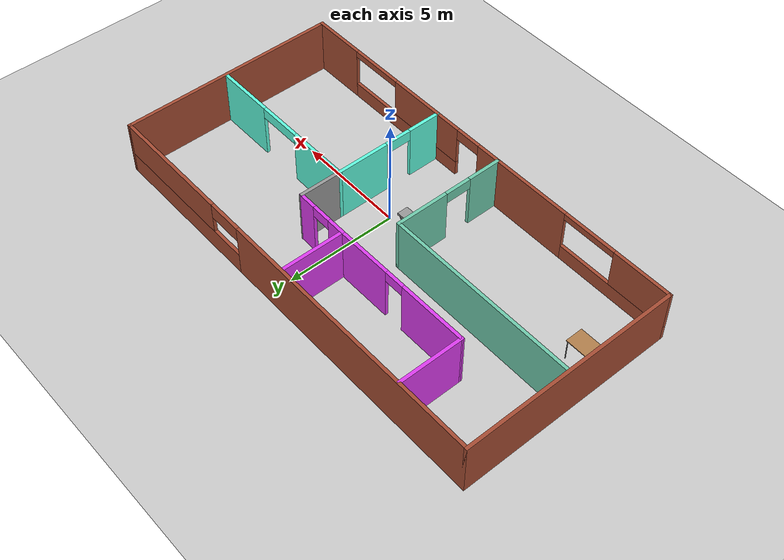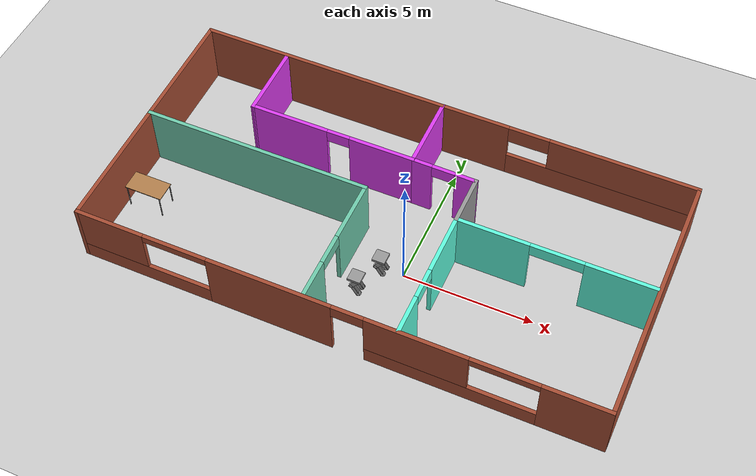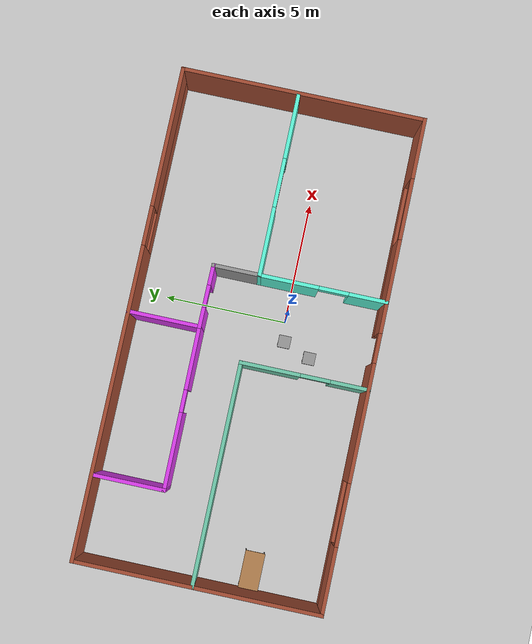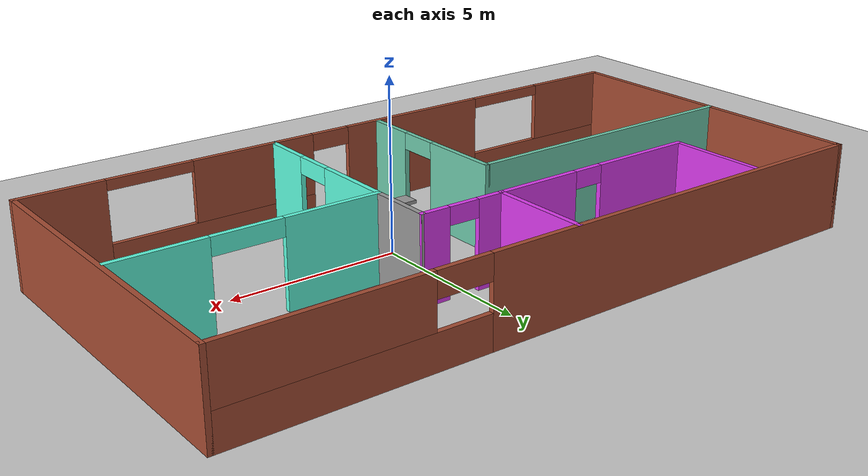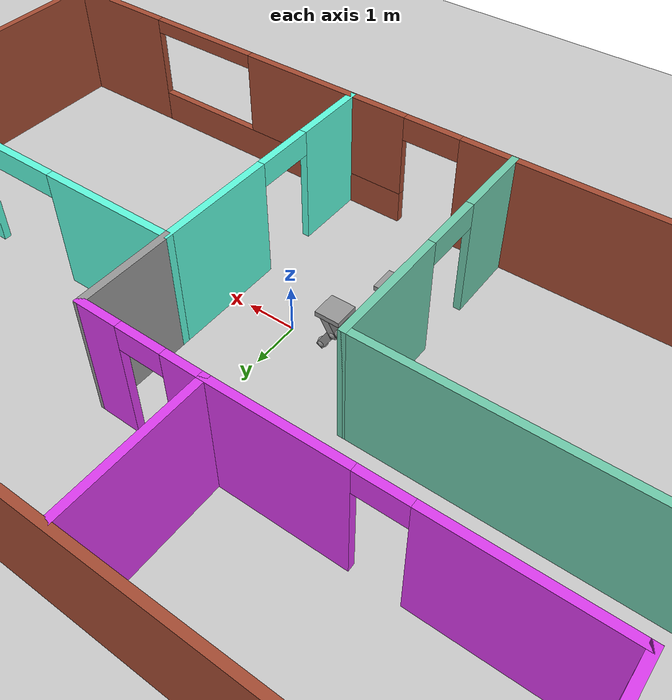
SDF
<sdf version="1.7">
 <world name="default">
  <plugin name="wecome" filename="libwelcome.so"/>
  <light name="sun" type="directional">
   <pose>0 0 10 0 -0 0</pose>
   <diffuse>0.8 0.8 0.8 1</diffuse>
   <specular>0.2 0.2 0.2 1</specular>
   <attenuation>
    <range>1000</range>
    <constant>0.9</constant>
    <linear>0.01</linear>
    <quadratic>0.001</quadratic>
   </attenuation>
   <direction>-0.5 0.1 -0.9</direction>
  </light>
  <model name="ground_plane">
   <static>1</static>
   <link name="link">
    <collision name="collision">
     <geometry><plane><normal>0 0 1</normal><size>100 100</size></plane></geometry>
     <surface>
      <contact><collide_bitmask>65535</collide_bitmask></contact>
      <friction><ode><mu>100</mu><mu2>50</mu2></ode></friction>
     </surface>
    </collision>
    <visual name="visual">
     <cast_shadows>0</cast_shadows>
     <geometry><plane><normal>0 0 1</normal><size>100 100</size></plane></geometry>
     <material>
      <script><uri>file://media/materials/scripts/gazebo.material</uri><name>Gazebo/Grey</name></script>
     </material>
    </visual>
   </link>
  </model>
  <gravity>0 0 -9.8</gravity>
  <magnetic_field>6e-06 2.3e-05 -4.2e-05</magnetic_field>
  <atmosphere type="adiabatic"/>
  <physics type="ode">
   <max_step_size>0.001</max_step_size>
   <real_time_factor>1</real_time_factor>
   <real_time_update_rate>1000</real_time_update_rate>
  </physics>
  <scene><ambient>0.4 0.4 0.4 1</ambient><background>0.7 0.7 0.7 1</background><shadows>1</shadows></scene>
  <spherical_coordinates>
   <surface_model>EARTH_WGS84</surface_model>
   <latitude_deg>0</latitude_deg>
   <longitude_deg>0</longitude_deg>
   <elevation>0</elevation>
   <heading_deg>0</heading_deg>
  </spherical_coordinates>
  <model name="Building1">
   <pose>-1.06781 1.2025 0 0 -0 0</pose>
   <link name="Wall_10">
    <collision name="Wall_10_Collision">
     <geometry><box><size>10 0.15 2.5</size></box></geometry>
     <pose>0 0 1.25 0 -0 0</pose>
    </collision>
    <visual name="Wall_10_Visual">
     <pose>0 0 1.25 0 -0 0</pose>
     <geometry><box><size>10 0.15 2.5</size></box></geometry>
     <material>
      <script><uri>file://media/materials/scripts/gazebo.material</uri><name>Gazebo/Bricks</name></script>
      <ambient>1 1 1 1</ambient>
     </material>
     <meta><layer>0</layer></meta>
    </visual>
    <pose>-9.925 0 0 0 -0 1.5708</pose>
   </link>
   <link name="Wall_12">
    <pose>-0 4.925 0 0 -0 0</pose>
    <visual name="Wall_12_Visual_0">
     <pose>-3.67331 0 1.25 0 -0 0</pose>
     <geometry><box><size>12.6534 0.15 2.5</size></box></geometry>
     <material>
      <script><uri>file://media/materials/scripts/gazebo.material</uri><name>Gazebo/Bricks</name></script>
      <ambient>1 1 1 1</ambient>
     </material>
     <meta><layer>0</layer></meta>
    </visual>
    <collision name="Wall_12_Collision_0">
     <geometry><box><size>12.6534 0.15 2.5</size></box></geometry>
     <pose>-3.67331 0 1.25 0 -0 0</pose>
    </collision>
    <visual name="Wall_12_Visual_1">
     <pose>6.32669 0 0.5 0 -0 0</pose>
     <geometry><box><size>7.34662 0.15 1</size></box></geometry>
     <material>
      <script><uri>file://media/materials/scripts/gazebo.material</uri><name>Gazebo/Bricks</name></script>
      <ambient>1 1 1 1</ambient>
     </material>
     <meta><layer>0</layer></meta>
    </visual>
    <collision name="Wall_12_Collision_1">
     <geometry><box><size>7.34662 0.15 1</size></box></geometry>
     <pose>6.32669 0 0.5 0 -0 0</pose>
    </collision>
    <visual name="Wall_12_Visual_2">
     <pose>7.12669 0 1.75 0 -0 0</pose>
     <geometry><box><size>5.74662 0.15 1.5</size></box></geometry>
     <material>
      <script><uri>file://media/materials/scripts/gazebo.material</uri><name>Gazebo/Bricks</name></script>
      <ambient>1 1 1 1</ambient>
     </material>
     <meta><layer>0</layer></meta>
    </visual>
    <collision name="Wall_12_Collision_2">
     <geometry><box><size>5.74662 0.15 1.5</size></box></geometry>
     <pose>7.12669 0 1.75 0 -0 0</pose>
    </collision>
    <visual name="Wall_12_Visual_3">
     <pose>3.45338 0 2.15 0 -0 0</pose>
     <geometry><box><size>1.6 0.15 0.7</size></box></geometry>
     <material>
      <script><uri>file://media/materials/scripts/gazebo.material</uri><name>Gazebo/Bricks</name></script>
      <ambient>1 1 1 1</ambient>
     </material>
     <meta><layer>0</layer></meta>
    </visual>
    <collision name="Wall_12_Collision_3">
     <geometry><box><size>1.6 0.15 0.7</size></box></geometry>
     <pose>3.45338 0 2.15 0 -0 0</pose>
    </collision>
   </link>
   <link name="Wall_13">
    <collision name="Wall_13_Collision">
     <geometry><box><size>10 0.15 2.5</size></box></geometry>
     <pose>0 0 1.25 0 -0 0</pose>
    </collision>
    <visual name="Wall_13_Visual">
     <pose>0 0 1.25 0 -0 0</pose>
     <geometry><box><size>10 0.15 2.5</size></box></geometry>
     <material>
      <script><uri>file://media/materials/scripts/gazebo.material</uri><name>Gazebo/Bricks</name></script>
      <ambient>1 1 1 1</ambient>
     </material>
     <meta><layer>0</layer></meta>
    </visual>
    <pose>9.925 0 0 0 -0 -1.5708</pose>
   </link>
   <link name="Wall_14">
    <pose>-0 -4.925 0 0 -0 3.14159</pose>
    <visual name="Wall_14_Visual_0">
     <pose>-8.75026 0 1.25 0 -0 0</pose>
     <geometry><box><size>2.49948 0.15 2.5</size></box></geometry>
     <material>
      <script><uri>file://media/materials/scripts/gazebo.material</uri><name>Gazebo/Bricks</name></script>
      <ambient>1 1 1 1</ambient>
     </material>
     <meta><layer>0</layer></meta>
    </visual>
    <collision name="Wall_14_Collision_0">
     <geometry><box><size>2.49948 0.15 2.5</size></box></geometry>
     <pose>-8.75026 0 1.25 0 -0 0</pose>
    </collision>
    <visual name="Wall_14_Visual_1">
     <pose>2.37306 0 1.25 0 -0 0</pose>
     <geometry><box><size>4.76763 0.15 2.5</size></box></geometry>
     <material>
      <script><uri>file://media/materials/scripts/gazebo.material</uri><name>Gazebo/Bricks</name></script>
      <ambient>1 1 1 1</ambient>
     </material>
     <meta><layer>0</layer></meta>
    </visual>
    <collision name="Wall_14_Collision_1">
     <geometry><box><size>4.76763 0.15 2.5</size></box></geometry>
     <pose>2.37306 0 1.25 0 -0 0</pose>
    </collision>
    <visual name="Wall_14_Visual_2">
     <pose>-4.35564 0 0.35 0 -0 0</pose>
     <geometry><box><size>6.28977 0.15 0.7</size></box></geometry>
     <material>
      <script><uri>file://media/materials/scripts/gazebo.material</uri><name>Gazebo/Bricks</name></script>
      <ambient>1 1 1 1</ambient>
     </material>
     <meta><layer>0</layer></meta>
    </visual>
    <collision name="Wall_14_Collision_2">
     <geometry><box><size>6.28977 0.15 0.7</size></box></geometry>
     <pose>-4.35564 0 0.35 0 -0 0</pose>
    </collision>
    <visual name="Wall_14_Visual_3">
     <pose>7.37844 0 0.35 0 -0 0</pose>
     <geometry><box><size>5.24313 0.15 0.7</size></box></geometry>
     <material>
      <script><uri>file://media/materials/scripts/gazebo.material</uri><name>Gazebo/Bricks</name></script>
      <ambient>1 1 1 1</ambient>
     </material>
     <meta><layer>0</layer></meta>
    </visual>
    <collision name="Wall_14_Collision_3">
     <geometry><box><size>5.24313 0.15 0.7</size></box></geometry>
     <pose>7.37844 0 0.35 0 -0 0</pose>
    </collision>
    <visual name="Wall_14_Visual_4">
     <pose>-3.10564 0 1.6 0 -0 0</pose>
     <geometry><box><size>3.78977 0.15 1.8</size></box></geometry>
     <material>
      <script><uri>file://media/materials/scripts/gazebo.material</uri><name>Gazebo/Bricks</name></script>
      <ambient>1 1 1 1</ambient>
     </material>
     <meta><layer>0</layer></meta>
    </visual>
    <collision name="Wall_14_Collision_4">
     <geometry><box><size>3.78977 0.15 1.8</size></box></geometry>
     <pose>-3.10564 0 1.6 0 -0 0</pose>
    </collision>
    <visual name="Wall_14_Visual_5">
     <pose>-3.10564 0 1.6 0 -0 0</pose>
     <geometry><box><size>3.78977 0.15 1.8</size></box></geometry>
     <material>
      <script><uri>file://media/materials/scripts/gazebo.material</uri><name>Gazebo/Bricks</name></script>
      <ambient>1 1 1 1</ambient>
     </material>
     <meta><layer>0</layer></meta>
    </visual>
    <collision name="Wall_14_Collision_5">
     <geometry><box><size>3.78977 0.15 1.8</size></box></geometry>
     <pose>-3.10564 0 1.6 0 -0 0</pose>
    </collision>
    <visual name="Wall_14_Visual_6">
     <pose>8.62844 0 1.6 0 -0 0</pose>
     <geometry><box><size>2.74313 0.15 1.8</size></box></geometry>
     <material>
      <script><uri>file://media/materials/scripts/gazebo.material</uri><name>Gazebo/Bricks</name></script>
      <ambient>1 1 1 1</ambient>
     </material>
     <meta><layer>0</layer></meta>
    </visual>
    <collision name="Wall_14_Collision_6">
     <geometry><box><size>2.74313 0.15 1.8</size></box></geometry>
     <pose>8.62844 0 1.6 0 -0 0</pose>
    </collision>
    <visual name="Wall_14_Visual_7">
     <pose>-0.610755 0 2.25 0 -0 0</pose>
     <geometry><box><size>1.2 0.15 0.5</size></box></geometry>
     <material>
      <script><uri>file://media/materials/scripts/gazebo.material</uri><name>Gazebo/Bricks</name></script>
      <ambient>1 1 1 1</ambient>
     </material>
     <meta><layer>0</layer></meta>
    </visual>
    <collision name="Wall_14_Collision_7">
     <geometry><box><size>1.2 0.15 0.5</size></box></geometry>
     <pose>-0.610755 0 2.25 0 -0 0</pose>
    </collision>
    <visual name="Wall_14_Visual_8">
     <pose>-0.610755 0 2.25 0 -0 0</pose>
     <geometry><box><size>1.2 0.15 0.5</size></box></geometry>
     <material>
      <script><uri>file://media/materials/scripts/gazebo.material</uri><name>Gazebo/Bricks</name></script>
      <ambient>1 1 1 1</ambient>
     </material>
     <meta><layer>0</layer></meta>
    </visual>
    <collision name="Wall_14_Collision_8">
     <geometry><box><size>1.2 0.15 0.5</size></box></geometry>
     <pose>-0.610755 0 2.25 0 -0 0</pose>
    </collision>
    <visual name="Wall_14_Visual_9">
     <pose>-6.25052 0 2.35 0 -0 0</pose>
     <geometry><box><size>2.5 0.15 0.3</size></box></geometry>
     <material>
      <script><uri>file://media/materials/scripts/gazebo.material</uri><name>Gazebo/Bricks</name></script>
      <ambient>1 1 1 1</ambient>
     </material>
     <meta><layer>0</layer></meta>
    </visual>
    <collision name="Wall_14_Collision_9">
     <geometry><box><size>2.5 0.15 0.3</size></box></geometry>
     <pose>-6.25052 0 2.35 0 -0 0</pose>
    </collision>
    <visual name="Wall_14_Visual_10">
     <pose>6.00687 0 2.35 0 -0 0</pose>
     <geometry><box><size>2.5 0.15 0.3</size></box></geometry>
     <material>
      <script><uri>file://media/materials/scripts/gazebo.material</uri><name>Gazebo/Bricks</name></script>
      <ambient>1 1 1 1</ambient>
     </material>
     <meta><layer>0</layer></meta>
    </visual>
    <collision name="Wall_14_Collision_10">
     <geometry><box><size>2.5 0.15 0.3</size></box></geometry>
     <pose>6.00687 0 2.35 0 -0 0</pose>
    </collision>
   </link>
   <link name="Wall_16">
    <collision name="Wall_16_Collision">
     <geometry><box><size>9 0.15 2.5</size></box></geometry>
     <pose>0 0 1.25 0 -0 0</pose>
    </collision>
    <visual name="Wall_16_Visual">
     <pose>0 0 1.25 0 -0 0</pose>
     <geometry><box><size>9 0.15 2.5</size></box></geometry>
     <material>
      <script><uri>file://media/materials/scripts/gazebo.material</uri><name>Gazebo/Grey</name></script>
      <ambient>0.435294 0.796078 0.67451 1</ambient>
     </material>
     <meta><layer>0</layer></meta>
    </visual>
    <pose>-5.4835 0.182385 0 0 -0 0</pose>
   </link>
   <link name="Wall_17">
    <pose>-1.0585 -2.36761 0 0 -0 -1.5708</pose>
    <visual name="Wall_17_Visual_0">
     <pose>-1.39742 0 1.25 0 -0 0</pose>
     <geometry><box><size>2.45515 0.15 2.5</size></box></geometry>
     <material>
      <script><uri>file://media/materials/scripts/gazebo.material</uri><name>Gazebo/Grey</name></script>
      <ambient>0.435294 0.796078 0.67451 1</ambient>
     </material>
     <meta><layer>0</layer></meta>
    </visual>
    <collision name="Wall_17_Collision_0">
     <geometry><box><size>2.45515 0.15 2.5</size></box></geometry>
     <pose>-1.39742 0 1.25 0 -0 0</pose>
    </collision>
    <visual name="Wall_17_Visual_1">
     <pose>1.82757 0 1.25 0 -0 0</pose>
     <geometry><box><size>1.59485 0.15 2.5</size></box></geometry>
     <material>
      <script><uri>file://media/materials/scripts/gazebo.material</uri><name>Gazebo/Grey</name></script>
      <ambient>0.435294 0.796078 0.67451 1</ambient>
     </material>
     <meta><layer>0</layer></meta>
    </visual>
    <collision name="Wall_17_Collision_1">
     <geometry><box><size>1.59485 0.15 2.5</size></box></geometry>
     <pose>1.82757 0 1.25 0 -0 0</pose>
    </collision>
    <visual name="Wall_17_Visual_2">
     <pose>0.430149 0 2.25 0 -0 0</pose>
     <geometry><box><size>1.2 0.15 0.5</size></box></geometry>
     <material>
      <script><uri>file://media/materials/scripts/gazebo.material</uri><name>Gazebo/Grey</name></script>
      <ambient>0.435294 0.796078 0.67451 1</ambient>
     </material>
     <meta><layer>0</layer></meta>
    </visual>
    <collision name="Wall_17_Collision_2">
     <geometry><box><size>1.2 0.15 0.5</size></box></geometry>
     <pose>0.430149 0 2.25 0 -0 0</pose>
    </collision>
   </link>
   <link name="Wall_19">
    <pose>6.13498 0.195027 0 0 -0 0</pose>
    <visual name="Wall_19_Visual_0">
     <pose>-2.3286 0 1.25 0 -0 0</pose>
     <geometry><box><size>2.8428 0.15 2.5</size></box></geometry>
     <material>
      <script><uri>file://media/materials/scripts/gazebo.material</uri><name>Gazebo/Grey</name></script>
      <ambient>0.372549 0.988235 0.870588 1</ambient>
     </material>
     <meta><layer>0</layer></meta>
    </visual>
    <collision name="Wall_19_Collision_0">
     <geometry><box><size>2.8428 0.15 2.5</size></box></geometry>
     <pose>-2.3286 0 1.25 0 -0 0</pose>
    </collision>
    <visual name="Wall_19_Visual_1">
     <pose>2.4214 0 1.25 0 -0 0</pose>
     <geometry><box><size>2.6572 0.15 2.5</size></box></geometry>
     <material>
      <script><uri>file://media/materials/scripts/gazebo.material</uri><name>Gazebo/Grey</name></script>
      <ambient>0.372549 0.988235 0.870588 1</ambient>
     </material>
     <meta><layer>0</layer></meta>
    </visual>
    <collision name="Wall_19_Collision_1">
     <geometry><box><size>2.6572 0.15 2.5</size></box></geometry>
     <pose>2.4214 0 1.25 0 -0 0</pose>
    </collision>
    <visual name="Wall_19_Visual_2">
     <pose>0.092803 0 2.25 0 -0 0</pose>
     <geometry><box><size>2 0.15 0.5</size></box></geometry>
     <material>
      <script><uri>file://media/materials/scripts/gazebo.material</uri><name>Gazebo/Grey</name></script>
      <ambient>0.372549 0.988235 0.870588 1</ambient>
     </material>
     <meta><layer>0</layer></meta>
    </visual>
    <collision name="Wall_19_Collision_2">
     <geometry><box><size>2 0.15 0.5</size></box></geometry>
     <pose>0.092803 0 2.25 0 -0 0</pose>
    </collision>
   </link>
   <link name="Wall_21">
    <pose>2.45998 -2.35497 0 0 -0 -1.5708</pose>
    <visual name="Wall_21_Visual_0">
     <pose>-1.3911 0 1.25 0 -0 0</pose>
     <geometry><box><size>2.46779 0.15 2.5</size></box></geometry>
     <material>
      <script><uri>file://media/materials/scripts/gazebo.material</uri><name>Gazebo/Grey</name></script>
      <ambient>0.372549 0.988235 0.870588 1</ambient>
     </material>
     <meta><layer>0</layer></meta>
    </visual>
    <collision name="Wall_21_Collision_0">
     <geometry><box><size>2.46779 0.15 2.5</size></box></geometry>
     <pose>-1.3911 0 1.25 0 -0 0</pose>
    </collision>
    <visual name="Wall_21_Visual_1">
     <pose>1.8339 0 1.25 0 -0 0</pose>
     <geometry><box><size>1.58221 0.15 2.5</size></box></geometry>
     <material>
      <script><uri>file://media/materials/scripts/gazebo.material</uri><name>Gazebo/Grey</name></script>
      <ambient>0.372549 0.988235 0.870588 1</ambient>
     </material>
     <meta><layer>0</layer></meta>
    </visual>
    <collision name="Wall_21_Collision_1">
     <geometry><box><size>1.58221 0.15 2.5</size></box></geometry>
     <pose>1.8339 0 1.25 0 -0 0</pose>
    </collision>
    <visual name="Wall_21_Visual_2">
     <pose>0.442791 0 2.25 0 -0 0</pose>
     <geometry><box><size>1.2 0.15 0.5</size></box></geometry>
     <material>
      <script><uri>file://media/materials/scripts/gazebo.material</uri><name>Gazebo/Grey</name></script>
      <ambient>0.372549 0.988235 0.870588 1</ambient>
     </material>
     <meta><layer>0</layer></meta>
    </visual>
    <collision name="Wall_21_Collision_2">
     <geometry><box><size>1.2 0.15 0.5</size></box></geometry>
     <pose>0.442791 0 2.25 0 -0 0</pose>
    </collision>
   </link>
   <link name="Wall_25">
    <collision name="Wall_25_Collision">
     <geometry><box><size>3 0.15 2.5</size></box></geometry>
     <pose>0 0 1.25 0 -0 0</pose>
    </collision>
    <visual name="Wall_25_Visual">
     <pose>0 0 1.25 0 -0 0</pose>
     <geometry><box><size>3 0.15 2.5</size></box></geometry>
     <material>
      <script><uri>file://media/materials/scripts/gazebo.material</uri><name>Gazebo/Grey</name></script>
      <ambient>0.870588 0.235294 0.941176 1</ambient>
     </material>
     <meta><layer>0</layer></meta>
    </visual>
    <pose>-6.53487 3.46477 0 0 -0 -1.5708</pose>
   </link>
   <link name="Wall_27">
    <collision name="Wall_27_Collision">
     <geometry><box><size>3 0.15 2.5</size></box></geometry>
     <pose>0 0 1.25 0 -0 0</pose>
    </collision>
    <visual name="Wall_27_Visual">
     <pose>0 0 1.25 0 -0 0</pose>
     <geometry><box><size>3 0.15 2.5</size></box></geometry>
     <material>
      <script><uri>file://media/materials/scripts/gazebo.material</uri><name>Gazebo/Grey</name></script>
      <ambient>0.870588 0.235294 0.941176 1</ambient>
     </material>
     <meta><layer>0</layer></meta>
    </visual>
    <pose>-0.02299 3.49092 0 0 -0 -1.5708</pose>
   </link>
   <link name="Wall_28">
    <pose>-3.27893 2.05285 0 0 -0 -3.13758</pose>
    <visual name="Wall_28_Visual_0">
     <pose>-2.02786 0 1.25 0 -0 0</pose>
     <geometry><box><size>2.60622 0.15 2.5</size></box></geometry>
     <material>
      <script><uri>file://media/materials/scripts/gazebo.material</uri><name>Gazebo/Grey</name></script>
      <ambient>0.870588 0.235294 0.941176 1</ambient>
     </material>
     <meta><layer>0</layer></meta>
    </visual>
    <collision name="Wall_28_Collision_0">
     <geometry><box><size>2.60622 0.15 2.5</size></box></geometry>
     <pose>-2.02786 0 1.25 0 -0 0</pose>
    </collision>
    <visual name="Wall_28_Visual_1">
     <pose>1.75311 0 1.25 0 -0 0</pose>
     <geometry><box><size>3.15572 0.15 2.5</size></box></geometry>
     <material>
      <script><uri>file://media/materials/scripts/gazebo.material</uri><name>Gazebo/Grey</name></script>
      <ambient>0.870588 0.235294 0.941176 1</ambient>
     </material>
     <meta><layer>0</layer></meta>
    </visual>
    <collision name="Wall_28_Collision_1">
     <geometry><box><size>3.15572 0.15 2.5</size></box></geometry>
     <pose>1.75311 0 1.25 0 -0 0</pose>
    </collision>
    <visual name="Wall_28_Visual_2">
     <pose>-0.274751 0 2.25 0 -0 0</pose>
     <geometry><box><size>0.9 0.15 0.5</size></box></geometry>
     <material>
      <script><uri>file://media/materials/scripts/gazebo.material</uri><name>Gazebo/Grey</name></script>
      <ambient>0.870588 0.235294 0.941176 1</ambient>
     </material>
     <meta><layer>0</layer></meta>
    </visual>
    <collision name="Wall_28_Collision_2">
     <geometry><box><size>0.9 0.15 0.5</size></box></geometry>
     <pose>-0.274751 0 2.25 0 -0 0</pose>
    </collision>
   </link>
   <link name="Wall_30">
    <collision name="Wall_30_Collision">
     <geometry><box><size>2 0.15 2.5</size></box></geometry>
     <pose>0 0 1.25 0 -0 0</pose>
    </collision>
    <visual name="Wall_30_Visual">
     <pose>0 0 1.25 0 -0 0</pose>
     <geometry><box><size>2 0.15 2.5</size></box></geometry>
     <material>
      <script><uri>file://media/materials/scripts/gazebo.material</uri><name>Gazebo/Grey</name></script>
      <ambient>1 1 1 1</ambient>
     </material>
     <meta><layer>0</layer></meta>
    </visual>
    <pose>2.45998 1.12003 0 0 -0 1.5708</pose>
   </link>
   <link name="Wall_31">
    <pose>1.21849 2.05547 0 0 -0 3.13318</pose>
    <visual name="Wall_31_Visual_0">
     <pose>-0.877056 0 1.25 0 -0 0</pose>
     <geometry><box><size>0.878942 0.15 2.5</size></box></geometry>
     <material>
      <script><uri>file://media/materials/scripts/gazebo.material</uri><name>Gazebo/Grey</name></script>
      <ambient>0.870588 0.235294 0.941176 1</ambient>
     </material>
     <meta><layer>0</layer></meta>
    </visual>
    <collision name="Wall_31_Collision_0">
     <geometry><box><size>0.878942 0.15 2.5</size></box></geometry>
     <pose>-0.877056 0 1.25 0 -0 0</pose>
    </collision>
    <visual name="Wall_31_Visual_1">
     <pose>0.889471 0 1.25 0 -0 0</pose>
     <geometry><box><size>0.854112 0.15 2.5</size></box></geometry>
     <material>
      <script><uri>file://media/materials/scripts/gazebo.material</uri><name>Gazebo/Grey</name></script>
      <ambient>0.870588 0.235294 0.941176 1</ambient>
     </material>
     <meta><layer>0</layer></meta>
    </visual>
    <collision name="Wall_31_Collision_1">
     <geometry><box><size>0.854112 0.15 2.5</size></box></geometry>
     <pose>0.889471 0 1.25 0 -0 0</pose>
    </collision>
    <visual name="Wall_31_Visual_2">
     <pose>0.012415 0 2.25 0 -0 0</pose>
     <geometry><box><size>0.9 0.15 0.5</size></box></geometry>
     <material>
      <script><uri>file://media/materials/scripts/gazebo.material</uri><name>Gazebo/Grey</name></script>
      <ambient>0.870588 0.235294 0.941176 1</ambient>
     </material>
     <meta><layer>0</layer></meta>
    </visual>
    <collision name="Wall_31_Collision_2">
     <geometry><box><size>0.9 0.15 0.5</size></box></geometry>
     <pose>0.012415 0 2.25 0 -0 0</pose>
    </collision>
   </link>
   <static>1</static>
  </model>
  <model name="2LeggedBot">
   <link name="link_0">
    <inertial>
     <mass>1</mass>
     <inertia><ixx>0.1</ixx><ixy>0</ixy><ixz>0</ixz><iyy>0.1</iyy><iyz>0</iyz><izz>0.1</izz></inertia>
    </inertial>
    <pose>0.169699 -0.170527 -0.315363 0 -0 0</pose>
    <visual name="visual">
     <geometry><sphere><radius>0.1</radius></sphere></geometry>
     <material>
      <lighting>1</lighting>
      <script><uri>file://media/materials/scripts/gazebo.material</uri><name>Gazebo/Grey</name></script>
      <shader type="pixel"><normal_map>__default__</normal_map></shader>
      <ambient>0.3 0.3 0.3 1</ambient>
      <diffuse>0.7 0.7 0.7 1</diffuse>
      <specular>0.01 0.01 0.01 1</specular>
      <emissive>0 0 0 1</emissive>
     </material>
    </visual>
    <visual name="ModelPreview_2::link_0::visual_1">
     <geometry><sphere><radius>0.1</radius></sphere></geometry>
     <material>
      <lighting>1</lighting>
      <script><uri>file://media/materials/scripts/gazebo.material</uri><name>Gazebo/Grey</name></script>
      <shader type="pixel"><normal_map>__default__</normal_map></shader>
      <ambient>0.3 0.3 0.3 1</ambient>
      <diffuse>0.7 0.7 0.7 1</diffuse>
      <specular>0.01 0.01 0.01 1</specular>
      <emissive>0 0 0 1</emissive>
     </material>
    </visual>
    <collision name="collision">
     <geometry><sphere><radius>0.1</radius></sphere></geometry>
     <surface>
      <friction>
       <ode><mu>1</mu><mu2>1</mu2><fdir1>0 0 0</fdir1><slip1>0</slip1><slip2>0</slip2></ode>
       <torsional>
        <coefficient>1</coefficient>
        <patch_radius>0</patch_radius>
        <surface_radius>0</surface_radius>
        <use_patch_radius>1</use_patch_radius>
        <ode><slip>0</slip></ode>
       </torsional>
      </friction>
      <bounce><restitution_coefficient>0</restitution_coefficient><threshold>1e+06</threshold></bounce>
      <contact>
       <collide_without_contact>0</collide_without_contact>
       <collide_without_contact_bitmask>1</collide_without_contact_bitmask>
       <collide_bitmask>1</collide_bitmask>
       <ode>
        <soft_cfm>0</soft_cfm>
        <soft_erp>0.2</soft_erp>
        <kp>1e+13</kp>
        <kd>1</kd>
        <max_vel>0.01</max_vel>
        <min_depth>0</min_depth>
       </ode>
       <bullet>
        <split_impulse>1</split_impulse>
        <split_impulse_penetration_threshold>-0.01</split_impulse_penetration_threshold>
        <soft_cfm>0</soft_cfm>
        <soft_erp>0.2</soft_erp>
        <kp>1e+13</kp>
        <kd>1</kd>
       </bullet>
      </contact>
     </surface>
    </collision>
   </link>
   <link name="link_0_clone">
    <inertial>
     <mass>1</mass>
     <inertia><ixx>0.1</ixx><ixy>0</ixy><ixz>0</ixz><iyy>0.1</iyy><iyz>0</iyz><izz>0.1</izz></inertia>
    </inertial>
    <pose>0.169699 0.129473 -0.315363 0 -0 0</pose>
    <visual name="visual">
     <geometry><sphere><radius>0.1</radius></sphere></geometry>
     <material>
      <lighting>1</lighting>
      <script><uri>file://media/materials/scripts/gazebo.material</uri><name>Gazebo/Grey</name></script>
      <shader type="pixel"><normal_map>__default__</normal_map></shader>
      <ambient>0.3 0.3 0.3 1</ambient>
      <diffuse>0.7 0.7 0.7 1</diffuse>
      <specular>0.01 0.01 0.01 1</specular>
      <emissive>0 0 0 1</emissive>
     </material>
    </visual>
    <visual name="visual_1">
     <geometry><sphere><radius>0.1</radius></sphere></geometry>
     <material>
      <lighting>1</lighting>
      <script><uri>file://media/materials/scripts/gazebo.material</uri><name>Gazebo/Grey</name></script>
      <shader type="pixel"><normal_map>__default__</normal_map></shader>
      <ambient>0.3 0.3 0.3 1</ambient>
      <diffuse>0.7 0.7 0.7 1</diffuse>
      <specular>0.01 0.01 0.01 1</specular>
      <emissive>0 0 0 1</emissive>
     </material>
    </visual>
    <collision name="collision">
     <geometry><sphere><radius>0.1</radius></sphere></geometry>
     <surface>
      <friction>
       <ode><mu>1</mu><mu2>1</mu2><fdir1>0 0 0</fdir1><slip1>0</slip1><slip2>0</slip2></ode>
       <torsional>
        <coefficient>1</coefficient>
        <patch_radius>0</patch_radius>
        <surface_radius>0</surface_radius>
        <use_patch_radius>1</use_patch_radius>
        <ode><slip>0</slip></ode>
       </torsional>
      </friction>
      <bounce><restitution_coefficient>0</restitution_coefficient><threshold>1e+06</threshold></bounce>
      <contact>
       <collide_without_contact>0</collide_without_contact>
       <collide_without_contact_bitmask>1</collide_without_contact_bitmask>
       <collide_bitmask>1</collide_bitmask>
       <ode>
        <soft_cfm>0</soft_cfm>
        <soft_erp>0.2</soft_erp>
        <kp>1e+13</kp>
        <kd>1</kd>
        <max_vel>0.01</max_vel>
        <min_depth>0</min_depth>
       </ode>
       <bullet>
        <split_impulse>1</split_impulse>
        <split_impulse_penetration_threshold>-0.01</split_impulse_penetration_threshold>
        <soft_cfm>0</soft_cfm>
        <soft_erp>0.2</soft_erp>
        <kp>1e+13</kp>
        <kd>1</kd>
       </bullet>
      </contact>
     </surface>
    </collision>
   </link>
   <link name="link_0_clone_0">
    <inertial>
     <mass>1</mass>
     <inertia><ixx>0.1</ixx><ixy>0</ixy><ixz>0</ixz><iyy>0.1</iyy><iyz>0</iyz><izz>0.1</izz></inertia>
    </inertial>
    <pose>-0.088021 0.142639 0.064349 0 -0 0</pose>
    <visual name="visual_1">
     <geometry><sphere><radius>0.1</radius></sphere></geometry>
     <material>
      <lighting>1</lighting>
      <script><uri>file://media/materials/scripts/gazebo.material</uri><name>Gazebo/Grey</name></script>
      <shader type="pixel"><normal_map>__default__</normal_map></shader>
      <ambient>0.3 0.3 0.3 1</ambient>
      <diffuse>0.7 0.7 0.7 1</diffuse>
      <specular>0.01 0.01 0.01 1</specular>
      <emissive>0 0 0 1</emissive>
     </material>
    </visual>
    <visual name="visual">
     <geometry><sphere><radius>0.1</radius></sphere></geometry>
     <material>
      <lighting>1</lighting>
      <script><uri>file://media/materials/scripts/gazebo.material</uri><name>Gazebo/Grey</name></script>
      <shader type="pixel"><normal_map>__default__</normal_map></shader>
      <ambient>0.3 0.3 0.3 1</ambient>
      <diffuse>0.7 0.7 0.7 1</diffuse>
      <specular>0.01 0.01 0.01 1</specular>
      <emissive>0 0 0 1</emissive>
     </material>
    </visual>
    <collision name="collision">
     <geometry><sphere><radius>0.1</radius></sphere></geometry>
     <surface>
      <friction>
       <ode><mu>1</mu><mu2>1</mu2><fdir1>0 0 0</fdir1><slip1>0</slip1><slip2>0</slip2></ode>
       <torsional>
        <coefficient>1</coefficient>
        <patch_radius>0</patch_radius>
        <surface_radius>0</surface_radius>
        <use_patch_radius>1</use_patch_radius>
        <ode><slip>0</slip></ode>
       </torsional>
      </friction>
      <bounce><restitution_coefficient>0</restitution_coefficient><threshold>1e+06</threshold></bounce>
      <contact>
       <collide_without_contact>0</collide_without_contact>
       <collide_without_contact_bitmask>1</collide_without_contact_bitmask>
       <collide_bitmask>1</collide_bitmask>
       <ode>
        <soft_cfm>0</soft_cfm>
        <soft_erp>0.2</soft_erp>
        <kp>1e+13</kp>
        <kd>1</kd>
        <max_vel>0.01</max_vel>
        <min_depth>0</min_depth>
       </ode>
       <bullet>
        <split_impulse>1</split_impulse>
        <split_impulse_penetration_threshold>-0.01</split_impulse_penetration_threshold>
        <soft_cfm>0</soft_cfm>
        <soft_erp>0.2</soft_erp>
        <kp>1e+13</kp>
        <kd>1</kd>
       </bullet>
      </contact>
     </surface>
    </collision>
   </link>
   <link name="link_0_clone_1">
    <inertial>
     <mass>1</mass>
     <inertia><ixx>0.1</ixx><ixy>0</ixy><ixz>0</ixz><iyy>0.1</iyy><iyz>0</iyz><izz>0.1</izz></inertia>
    </inertial>
    <pose>-0.092915 -0.172952 0.04398 0 -0 0</pose>
    <visual name="visual">
     <geometry><sphere><radius>0.1</radius></sphere></geometry>
     <material>
      <lighting>1</lighting>
      <script><uri>file://media/materials/scripts/gazebo.material</uri><name>Gazebo/Grey</name></script>
      <shader type="pixel"><normal_map>__default__</normal_map></shader>
      <ambient>0.3 0.3 0.3 1</ambient>
      <diffuse>0.7 0.7 0.7 1</diffuse>
      <specular>0.01 0.01 0.01 1</specular>
      <emissive>0 0 0 1</emissive>
     </material>
    </visual>
    <visual name="visual_1">
     <geometry><sphere><radius>0.1</radius></sphere></geometry>
     <material>
      <lighting>1</lighting>
      <script><uri>file://media/materials/scripts/gazebo.material</uri><name>Gazebo/Grey</name></script>
      <shader type="pixel"><normal_map>__default__</normal_map></shader>
      <ambient>0.3 0.3 0.3 1</ambient>
      <diffuse>0.7 0.7 0.7 1</diffuse>
      <specular>0.01 0.01 0.01 1</specular>
      <emissive>0 0 0 1</emissive>
     </material>
    </visual>
    <collision name="collision">
     <geometry><sphere><radius>0.1</radius></sphere></geometry>
     <surface>
      <friction>
       <ode><mu>1</mu><mu2>1</mu2><fdir1>0 0 0</fdir1><slip1>0</slip1><slip2>0</slip2></ode>
       <torsional>
        <coefficient>1</coefficient>
        <patch_radius>0</patch_radius>
        <surface_radius>0</surface_radius>
        <use_patch_radius>1</use_patch_radius>
        <ode><slip>0</slip></ode>
       </torsional>
      </friction>
      <bounce><restitution_coefficient>0</restitution_coefficient><threshold>1e+06</threshold></bounce>
      <contact>
       <collide_without_contact>0</collide_without_contact>
       <collide_without_contact_bitmask>1</collide_without_contact_bitmask>
       <collide_bitmask>1</collide_bitmask>
       <ode>
        <soft_cfm>0</soft_cfm>
        <soft_erp>0.2</soft_erp>
        <kp>1e+13</kp>
        <kd>1</kd>
        <max_vel>0.01</max_vel>
        <min_depth>0</min_depth>
       </ode>
       <bullet>
        <split_impulse>1</split_impulse>
        <split_impulse_penetration_threshold>-0.01</split_impulse_penetration_threshold>
        <soft_cfm>0</soft_cfm>
        <soft_erp>0.2</soft_erp>
        <kp>1e+13</kp>
        <kd>1</kd>
       </bullet>
      </contact>
     </surface>
    </collision>
   </link>
   <link name="link_2">
    <inertial>
     <mass>1</mass>
     <inertia>
      <ixx>0.166667</ixx>
      <ixy>0</ixy>
      <ixz>0</ixz>
      <iyy>0.166667</iyy>
      <iyz>0</iyz>
      <izz>0.166667</izz>
     </inertia>
    </inertial>
    <pose>0.063484 -0.170527 -0.161345 0 -0.5234 0</pose>
    <visual name="visual">
     <geometry><box><size>0.15 0.15 0.5</size></box></geometry>
     <material>
      <lighting>1</lighting>
      <script><uri>file://media/materials/scripts/gazebo.material</uri><name>Gazebo/Grey</name></script>
      <shader type="pixel"><normal_map>__default__</normal_map></shader>
      <ambient>0.3 0.3 0.3 1</ambient>
      <diffuse>0.7 0.7 0.7 1</diffuse>
      <specular>0.01 0.01 0.01 1</specular>
      <emissive>0 0 0 1</emissive>
     </material>
    </visual>
    <collision name="collision">
     <geometry><box><size>0.15 0.15 0.5</size></box></geometry>
     <surface>
      <friction>
       <ode><mu>1</mu><mu2>1</mu2><fdir1>0 0 0</fdir1><slip1>0</slip1><slip2>0</slip2></ode>
       <torsional>
        <coefficient>1</coefficient>
        <patch_radius>0</patch_radius>
        <surface_radius>0</surface_radius>
        <use_patch_radius>1</use_patch_radius>
        <ode><slip>0</slip></ode>
       </torsional>
      </friction>
      <bounce><restitution_coefficient>0</restitution_coefficient><threshold>1e+06</threshold></bounce>
      <contact>
       <collide_without_contact>0</collide_without_contact>
       <collide_without_contact_bitmask>1</collide_without_contact_bitmask>
       <collide_bitmask>1</collide_bitmask>
       <ode>
        <soft_cfm>0</soft_cfm>
        <soft_erp>0.2</soft_erp>
        <kp>1e+13</kp>
        <kd>1</kd>
        <max_vel>0.01</max_vel>
        <min_depth>0</min_depth>
       </ode>
       <bullet>
        <split_impulse>1</split_impulse>
        <split_impulse_penetration_threshold>-0.01</split_impulse_penetration_threshold>
        <soft_cfm>0</soft_cfm>
        <soft_erp>0.2</soft_erp>
        <kp>1e+13</kp>
        <kd>1</kd>
       </bullet>
      </contact>
     </surface>
    </collision>
   </link>
   <link name="link_2_clone">
    <inertial>
     <mass>1</mass>
     <inertia>
      <ixx>0.166667</ixx>
      <ixy>0</ixy>
      <ixz>0</ixz>
      <iyy>0.166667</iyy>
      <iyz>0</iyz>
      <izz>0.166667</izz>
     </inertia>
    </inertial>
    <pose>0.001286 0.142639 0.21857 0 0.52 0</pose>
    <visual name="visual">
     <geometry><box><size>0.15 0.15 0.5</size></box></geometry>
     <material>
      <lighting>1</lighting>
      <script><uri>file://media/materials/scripts/gazebo.material</uri><name>Gazebo/Grey</name></script>
      <shader type="pixel"><normal_map>__default__</normal_map></shader>
      <ambient>0.3 0.3 0.3 1</ambient>
      <diffuse>0.7 0.7 0.7 1</diffuse>
      <specular>0.01 0.01 0.01 1</specular>
      <emissive>0 0 0 1</emissive>
     </material>
    </visual>
    <collision name="collision">
     <geometry><box><size>0.15 0.15 0.5</size></box></geometry>
     <surface>
      <friction>
       <ode><mu>1</mu><mu2>1</mu2><fdir1>0 0 0</fdir1><slip1>0</slip1><slip2>0</slip2></ode>
       <torsional>
        <coefficient>1</coefficient>
        <patch_radius>0</patch_radius>
        <surface_radius>0</surface_radius>
        <use_patch_radius>1</use_patch_radius>
        <ode><slip>0</slip></ode>
       </torsional>
      </friction>
      <bounce><restitution_coefficient>0</restitution_coefficient><threshold>1e+06</threshold></bounce>
      <contact>
       <collide_without_contact>0</collide_without_contact>
       <collide_without_contact_bitmask>1</collide_without_contact_bitmask>
       <collide_bitmask>1</collide_bitmask>
       <ode>
        <soft_cfm>0</soft_cfm>
        <soft_erp>0.2</soft_erp>
        <kp>1e+13</kp>
        <kd>1</kd>
        <max_vel>0.01</max_vel>
        <min_depth>0</min_depth>
       </ode>
       <bullet>
        <split_impulse>1</split_impulse>
        <split_impulse_penetration_threshold>-0.01</split_impulse_penetration_threshold>
        <soft_cfm>0</soft_cfm>
        <soft_erp>0.2</soft_erp>
        <kp>1e+13</kp>
        <kd>1</kd>
       </bullet>
      </contact>
     </surface>
    </collision>
   </link>
   <link name="link_2_clone_0">
    <inertial>
     <mass>1</mass>
     <inertia>
      <ixx>0.166667</ixx>
      <ixy>0</ixy>
      <ixz>0</ixz>
      <iyy>0.166667</iyy>
      <iyz>0</iyz>
      <izz>0.166667</izz>
     </inertia>
    </inertial>
    <pose>0.079782 0.129473 -0.161345 0 -0.5234 0</pose>
    <visual name="visual">
     <geometry><box><size>0.15 0.15 0.5</size></box></geometry>
     <material>
      <lighting>1</lighting>
      <script><uri>file://media/materials/scripts/gazebo.material</uri><name>Gazebo/Grey</name></script>
      <shader type="pixel"><normal_map>__default__</normal_map></shader>
      <ambient>0.3 0.3 0.3 1</ambient>
      <diffuse>0.7 0.7 0.7 1</diffuse>
      <specular>0.01 0.01 0.01 1</specular>
      <emissive>0 0 0 1</emissive>
     </material>
    </visual>
    <collision name="collision">
     <geometry><box><size>0.15 0.15 0.5</size></box></geometry>
     <surface>
      <friction>
       <ode><mu>1</mu><mu2>1</mu2><fdir1>0 0 0</fdir1><slip1>0</slip1><slip2>0</slip2></ode>
       <torsional>
        <coefficient>1</coefficient>
        <patch_radius>0</patch_radius>
        <surface_radius>0</surface_radius>
        <use_patch_radius>1</use_patch_radius>
        <ode><slip>0</slip></ode>
       </torsional>
      </friction>
      <bounce><restitution_coefficient>0</restitution_coefficient><threshold>1e+06</threshold></bounce>
      <contact>
       <collide_without_contact>0</collide_without_contact>
       <collide_without_contact_bitmask>1</collide_without_contact_bitmask>
       <collide_bitmask>1</collide_bitmask>
       <ode>
        <soft_cfm>0</soft_cfm>
        <soft_erp>0.2</soft_erp>
        <kp>1e+13</kp>
        <kd>1</kd>
        <max_vel>0.01</max_vel>
        <min_depth>0</min_depth>
       </ode>
       <bullet>
        <split_impulse>1</split_impulse>
        <split_impulse_penetration_threshold>-0.01</split_impulse_penetration_threshold>
        <soft_cfm>0</soft_cfm>
        <soft_erp>0.2</soft_erp>
        <kp>1e+13</kp>
        <kd>1</kd>
       </bullet>
      </contact>
     </surface>
    </collision>
   </link>
   <link name="link_2_clone_clone">
    <inertial>
     <mass>1</mass>
     <inertia>
      <ixx>0.166667</ixx>
      <ixy>0</ixy>
      <ixz>0</ixz>
      <iyy>0.166667</iyy>
      <iyz>0</iyz>
      <izz>0.166667</izz>
     </inertia>
    </inertial>
    <pose>-0.003609 -0.172952 0.1982 0 0.52 0</pose>
    <visual name="visual">
     <geometry><box><size>0.15 0.15 0.5</size></box></geometry>
     <material>
      <lighting>1</lighting>
      <script><uri>file://media/materials/scripts/gazebo.material</uri><name>Gazebo/Grey</name></script>
      <shader type="pixel"><normal_map>__default__</normal_map></shader>
      <ambient>0.3 0.3 0.3 1</ambient>
      <diffuse>0.7 0.7 0.7 1</diffuse>
      <specular>0.01 0.01 0.01 1</specular>
      <emissive>0 0 0 1</emissive>
     </material>
    </visual>
    <collision name="collision">
     <geometry><box><size>0.15 0.15 0.5</size></box></geometry>
     <surface>
      <friction>
       <ode><mu>1</mu><mu2>1</mu2><fdir1>0 0 0</fdir1><slip1>0</slip1><slip2>0</slip2></ode>
       <torsional>
        <coefficient>1</coefficient>
        <patch_radius>0</patch_radius>
        <surface_radius>0</surface_radius>
        <use_patch_radius>1</use_patch_radius>
        <ode><slip>0</slip></ode>
       </torsional>
      </friction>
      <bounce><restitution_coefficient>0</restitution_coefficient><threshold>1e+06</threshold></bounce>
      <contact>
       <collide_without_contact>0</collide_without_contact>
       <collide_without_contact_bitmask>1</collide_without_contact_bitmask>
       <collide_bitmask>1</collide_bitmask>
       <ode>
        <soft_cfm>0</soft_cfm>
        <soft_erp>0.2</soft_erp>
        <kp>1e+13</kp>
        <kd>1</kd>
        <max_vel>0.01</max_vel>
        <min_depth>0</min_depth>
       </ode>
       <bullet>
        <split_impulse>1</split_impulse>
        <split_impulse_penetration_threshold>-0.01</split_impulse_penetration_threshold>
        <soft_cfm>0</soft_cfm>
        <soft_erp>0.2</soft_erp>
        <kp>1e+13</kp>
        <kd>1</kd>
       </bullet>
      </contact>
     </surface>
    </collision>
   </link>
   <link name="link_3">
    <inertial>
     <mass>1</mass>
     <inertia>
      <ixx>0.166667</ixx>
      <ixy>0</ixy>
      <ixz>0</ixz>
      <iyy>0.166667</iyy>
      <iyz>0</iyz>
      <izz>0.166667</izz>
     </inertia>
    </inertial>
    <pose>0.014885 -0.015108 0.428317 0 -0 0</pose>
    <visual name="visual">
     <geometry><box><size>0.5 0.5 0.1</size></box></geometry>
     <material>
      <lighting>1</lighting>
      <script><uri>file://media/materials/scripts/gazebo.material</uri><name>Gazebo/Grey</name></script>
      <shader type="pixel"><normal_map>__default__</normal_map></shader>
      <ambient>0.3 0.3 0.3 1</ambient>
      <diffuse>0.7 0.7 0.7 1</diffuse>
      <specular>0.01 0.01 0.01 1</specular>
      <emissive>0 0 0 1</emissive>
     </material>
    </visual>
    <collision name="collision">
     <geometry><box><size>0.5 0.5 0.1</size></box></geometry>
     <surface>
      <friction>
       <ode><mu>1</mu><mu2>1</mu2><fdir1>0 0 0</fdir1><slip1>0</slip1><slip2>0</slip2></ode>
       <torsional>
        <coefficient>1</coefficient>
        <patch_radius>0</patch_radius>
        <surface_radius>0</surface_radius>
        <use_patch_radius>1</use_patch_radius>
        <ode><slip>0</slip></ode>
       </torsional>
      </friction>
      <bounce><restitution_coefficient>0</restitution_coefficient><threshold>1e+06</threshold></bounce>
      <contact>
       <collide_without_contact>0</collide_without_contact>
       <collide_without_contact_bitmask>1</collide_without_contact_bitmask>
       <collide_bitmask>1</collide_bitmask>
       <ode>
        <soft_cfm>0</soft_cfm>
        <soft_erp>0.2</soft_erp>
        <kp>1e+13</kp>
        <kd>1</kd>
        <max_vel>0.01</max_vel>
        <min_depth>0</min_depth>
       </ode>
       <bullet>
        <split_impulse>1</split_impulse>
        <split_impulse_penetration_threshold>-0.01</split_impulse_penetration_threshold>
        <soft_cfm>0</soft_cfm>
        <soft_erp>0.2</soft_erp>
        <kp>1e+13</kp>
        <kd>1</kd>
       </bullet>
      </contact>
     </surface>
    </collision>
   </link>
   <joint name="link_0_clone_0_JOINT_4" type="revolute">
    <parent>link_0_clone_0</parent>
    <child>link_2_clone</child>
    <axis>
     <xyz>1 0 0</xyz>
     <limit>
      <lower>-1.79769e+308</lower>
      <upper>1.79769e+308</upper>
      <effort>-1</effort>
      <velocity>-1</velocity>
     </limit>
     <dynamics>
      <spring_reference>0</spring_reference>
      <spring_stiffness>0</spring_stiffness>
      <damping>0</damping>
      <friction>0</friction>
     </dynamics>
    </axis>
    <physics>
     <ode><limit><cfm>0</cfm><erp>0.2</erp></limit><suspension><cfm>0</cfm><erp>0.2</erp></suspension></ode>
    </physics>
   </joint>
   <joint name="link_0_clone_1_JOINT_5" type="revolute">
    <parent>link_0_clone_1</parent>
    <child>link_2_clone_clone</child>
    <axis>
     <xyz>1 0 0</xyz>
     <limit>
      <lower>-1.79769e+308</lower>
      <upper>1.79769e+308</upper>
      <effort>-1</effort>
      <velocity>-1</velocity>
     </limit>
     <dynamics>
      <spring_reference>0</spring_reference>
      <spring_stiffness>0</spring_stiffness>
      <damping>0</damping>
      <friction>0</friction>
     </dynamics>
    </axis>
    <physics>
     <ode><limit><cfm>0</cfm><erp>0.2</erp></limit><suspension><cfm>0</cfm><erp>0.2</erp></suspension></ode>
    </physics>
   </joint>
   <joint name="link_0_clone_JOINT_1" type="fixed">
    <parent>link_0_clone</parent>
    <child>link_2_clone_0</child>
    <physics>
     <ode><limit><cfm>0</cfm><erp>0.2</erp></limit><suspension><cfm>0</cfm><erp>0.2</erp></suspension></ode>
    </physics>
   </joint>
   <joint name="link_2_JOINT_0" type="fixed">
    <parent>link_0</parent>
    <child>link_2</child>
    <physics>
     <ode><limit><cfm>0</cfm><erp>0.2</erp></limit><suspension><cfm>0</cfm><erp>0.2</erp></suspension></ode>
    </physics>
   </joint>
   <joint name="link_2_JOINT_2" type="revolute">
    <parent>link_2</parent>
    <child>link_0_clone_1</child>
    <axis>
     <xyz>1 0 0</xyz>
     <limit>
      <lower>-1.79769e+308</lower>
      <upper>1.79769e+308</upper>
      <effort>-1</effort>
      <velocity>-1</velocity>
     </limit>
     <dynamics>
      <spring_reference>0</spring_reference>
      <spring_stiffness>0</spring_stiffness>
      <damping>0</damping>
      <friction>0</friction>
     </dynamics>
    </axis>
    <physics>
     <ode><limit><cfm>0</cfm><erp>0.2</erp></limit><suspension><cfm>0</cfm><erp>0.2</erp></suspension></ode>
    </physics>
   </joint>
   <joint name="link_2_clone_0_JOINT_3" type="fixed">
    <parent>link_2_clone_0</parent>
    <child>link_0_clone_0</child>
    <physics>
     <ode><limit><cfm>0</cfm><erp>0.2</erp></limit><suspension><cfm>0</cfm><erp>0.2</erp></suspension></ode>
    </physics>
   </joint>
   <joint name="link_2_clone_JOINT_8" type="fixed">
    <parent>link_2_clone</parent>
    <child>link_3</child>
    <physics>
     <ode><limit><cfm>0</cfm><erp>0.2</erp></limit><suspension><cfm>0</cfm><erp>0.2</erp></suspension></ode>
    </physics>
   </joint>
   <joint name="link_3_JOINT_7" type="fixed">
    <parent>link_3</parent>
    <child>link_2_clone_clone</child>
    <physics>
     <ode><limit><cfm>0</cfm><erp>0.2</erp></limit><suspension><cfm>0</cfm><erp>0.2</erp></suspension></ode>
    </physics>
   </joint>
   <static>1</static>
   <pose>-0.864417 -0.116722 0.422143 0 -0 0</pose>
  </model>
  <model name="2LeggedBot_clone">
   <link name="link_0">
    <inertial>
     <mass>1</mass>
     <inertia><ixx>0.1</ixx><ixy>0</ixy><ixz>0</ixz><iyy>0.1</iyy><iyz>0</iyz><izz>0.1</izz></inertia>
    </inertial>
    <pose>0.169699 -0.170527 -0.315363 0 -0 0</pose>
    <visual name="visual">
     <geometry><sphere><radius>0.1</radius></sphere></geometry>
     <material>
      <lighting>1</lighting>
      <script><uri>file://media/materials/scripts/gazebo.material</uri><name>Gazebo/Grey</name></script>
      <shader type="pixel"><normal_map>__default__</normal_map></shader>
      <ambient>0.3 0.3 0.3 1</ambient>
      <diffuse>0.7 0.7 0.7 1</diffuse>
      <specular>0.01 0.01 0.01 1</specular>
      <emissive>0 0 0 1</emissive>
     </material>
    </visual>
    <visual name="ModelPreview_2::link_0::visual_1">
     <geometry><sphere><radius>0.1</radius></sphere></geometry>
     <material>
      <lighting>1</lighting>
      <script><uri>file://media/materials/scripts/gazebo.material</uri><name>Gazebo/Grey</name></script>
      <shader type="pixel"><normal_map>__default__</normal_map></shader>
      <ambient>0.3 0.3 0.3 1</ambient>
      <diffuse>0.7 0.7 0.7 1</diffuse>
      <specular>0.01 0.01 0.01 1</specular>
      <emissive>0 0 0 1</emissive>
     </material>
    </visual>
    <collision name="collision">
     <geometry><sphere><radius>0.1</radius></sphere></geometry>
     <surface>
      <friction>
       <ode><mu>1</mu><mu2>1</mu2><fdir1>0 0 0</fdir1><slip1>0</slip1><slip2>0</slip2></ode>
       <torsional>
        <coefficient>1</coefficient>
        <patch_radius>0</patch_radius>
        <surface_radius>0</surface_radius>
        <use_patch_radius>1</use_patch_radius>
        <ode><slip>0</slip></ode>
       </torsional>
      </friction>
      <bounce><restitution_coefficient>0</restitution_coefficient><threshold>1e+06</threshold></bounce>
      <contact>
       <collide_without_contact>0</collide_without_contact>
       <collide_without_contact_bitmask>1</collide_without_contact_bitmask>
       <collide_bitmask>1</collide_bitmask>
       <ode>
        <soft_cfm>0</soft_cfm>
        <soft_erp>0.2</soft_erp>
        <kp>1e+13</kp>
        <kd>1</kd>
        <max_vel>0.01</max_vel>
        <min_depth>0</min_depth>
       </ode>
       <bullet>
        <split_impulse>1</split_impulse>
        <split_impulse_penetration_threshold>-0.01</split_impulse_penetration_threshold>
        <soft_cfm>0</soft_cfm>
        <soft_erp>0.2</soft_erp>
        <kp>1e+13</kp>
        <kd>1</kd>
       </bullet>
      </contact>
     </surface>
    </collision>
   </link>
   <link name="link_0_clone">
    <inertial>
     <mass>1</mass>
     <inertia><ixx>0.1</ixx><ixy>0</ixy><ixz>0</ixz><iyy>0.1</iyy><iyz>0</iyz><izz>0.1</izz></inertia>
    </inertial>
    <pose>0.169699 0.129473 -0.315363 0 -0 0</pose>
    <visual name="visual">
     <geometry><sphere><radius>0.1</radius></sphere></geometry>
     <material>
      <lighting>1</lighting>
      <script><uri>file://media/materials/scripts/gazebo.material</uri><name>Gazebo/Grey</name></script>
      <shader type="pixel"><normal_map>__default__</normal_map></shader>
      <ambient>0.3 0.3 0.3 1</ambient>
      <diffuse>0.7 0.7 0.7 1</diffuse>
      <specular>0.01 0.01 0.01 1</specular>
      <emissive>0 0 0 1</emissive>
     </material>
    </visual>
    <visual name="visual_1">
     <geometry><sphere><radius>0.1</radius></sphere></geometry>
     <material>
      <lighting>1</lighting>
      <script><uri>file://media/materials/scripts/gazebo.material</uri><name>Gazebo/Grey</name></script>
      <shader type="pixel"><normal_map>__default__</normal_map></shader>
      <ambient>0.3 0.3 0.3 1</ambient>
      <diffuse>0.7 0.7 0.7 1</diffuse>
      <specular>0.01 0.01 0.01 1</specular>
      <emissive>0 0 0 1</emissive>
     </material>
    </visual>
    <collision name="collision">
     <geometry><sphere><radius>0.1</radius></sphere></geometry>
     <surface>
      <friction>
       <ode><mu>1</mu><mu2>1</mu2><fdir1>0 0 0</fdir1><slip1>0</slip1><slip2>0</slip2></ode>
       <torsional>
        <coefficient>1</coefficient>
        <patch_radius>0</patch_radius>
        <surface_radius>0</surface_radius>
        <use_patch_radius>1</use_patch_radius>
        <ode><slip>0</slip></ode>
       </torsional>
      </friction>
      <bounce><restitution_coefficient>0</restitution_coefficient><threshold>1e+06</threshold></bounce>
      <contact>
       <collide_without_contact>0</collide_without_contact>
       <collide_without_contact_bitmask>1</collide_without_contact_bitmask>
       <collide_bitmask>1</collide_bitmask>
       <ode>
        <soft_cfm>0</soft_cfm>
        <soft_erp>0.2</soft_erp>
        <kp>1e+13</kp>
        <kd>1</kd>
        <max_vel>0.01</max_vel>
        <min_depth>0</min_depth>
       </ode>
       <bullet>
        <split_impulse>1</split_impulse>
        <split_impulse_penetration_threshold>-0.01</split_impulse_penetration_threshold>
        <soft_cfm>0</soft_cfm>
        <soft_erp>0.2</soft_erp>
        <kp>1e+13</kp>
        <kd>1</kd>
       </bullet>
      </contact>
     </surface>
    </collision>
   </link>
   <link name="link_0_clone_0">
    <inertial>
     <mass>1</mass>
     <inertia><ixx>0.1</ixx><ixy>0</ixy><ixz>0</ixz><iyy>0.1</iyy><iyz>0</iyz><izz>0.1</izz></inertia>
    </inertial>
    <pose>-0.088021 0.142639 0.064349 0 -0 0</pose>
    <visual name="visual_1">
     <geometry><sphere><radius>0.1</radius></sphere></geometry>
     <material>
      <lighting>1</lighting>
      <script><uri>file://media/materials/scripts/gazebo.material</uri><name>Gazebo/Grey</name></script>
      <shader type="pixel"><normal_map>__default__</normal_map></shader>
      <ambient>0.3 0.3 0.3 1</ambient>
      <diffuse>0.7 0.7 0.7 1</diffuse>
      <specular>0.01 0.01 0.01 1</specular>
      <emissive>0 0 0 1</emissive>
     </material>
    </visual>
    <visual name="visual">
     <geometry><sphere><radius>0.1</radius></sphere></geometry>
     <material>
      <lighting>1</lighting>
      <script><uri>file://media/materials/scripts/gazebo.material</uri><name>Gazebo/Grey</name></script>
      <shader type="pixel"><normal_map>__default__</normal_map></shader>
      <ambient>0.3 0.3 0.3 1</ambient>
      <diffuse>0.7 0.7 0.7 1</diffuse>
      <specular>0.01 0.01 0.01 1</specular>
      <emissive>0 0 0 1</emissive>
     </material>
    </visual>
    <collision name="collision">
     <geometry><sphere><radius>0.1</radius></sphere></geometry>
     <surface>
      <friction>
       <ode><mu>1</mu><mu2>1</mu2><fdir1>0 0 0</fdir1><slip1>0</slip1><slip2>0</slip2></ode>
       <torsional>
        <coefficient>1</coefficient>
        <patch_radius>0</patch_radius>
        <surface_radius>0</surface_radius>
        <use_patch_radius>1</use_patch_radius>
        <ode><slip>0</slip></ode>
       </torsional>
      </friction>
      <bounce><restitution_coefficient>0</restitution_coefficient><threshold>1e+06</threshold></bounce>
      <contact>
       <collide_without_contact>0</collide_without_contact>
       <collide_without_contact_bitmask>1</collide_without_contact_bitmask>
       <collide_bitmask>1</collide_bitmask>
       <ode>
        <soft_cfm>0</soft_cfm>
        <soft_erp>0.2</soft_erp>
        <kp>1e+13</kp>
        <kd>1</kd>
        <max_vel>0.01</max_vel>
        <min_depth>0</min_depth>
       </ode>
       <bullet>
        <split_impulse>1</split_impulse>
        <split_impulse_penetration_threshold>-0.01</split_impulse_penetration_threshold>
        <soft_cfm>0</soft_cfm>
        <soft_erp>0.2</soft_erp>
        <kp>1e+13</kp>
        <kd>1</kd>
       </bullet>
      </contact>
     </surface>
    </collision>
   </link>
   <link name="link_0_clone_1">
    <inertial>
     <mass>1</mass>
     <inertia><ixx>0.1</ixx><ixy>0</ixy><ixz>0</ixz><iyy>0.1</iyy><iyz>0</iyz><izz>0.1</izz></inertia>
    </inertial>
    <pose>-0.092915 -0.172952 0.04398 0 -0 0</pose>
    <visual name="visual">
     <geometry><sphere><radius>0.1</radius></sphere></geometry>
     <material>
      <lighting>1</lighting>
      <script><uri>file://media/materials/scripts/gazebo.material</uri><name>Gazebo/Grey</name></script>
      <shader type="pixel"><normal_map>__default__</normal_map></shader>
      <ambient>0.3 0.3 0.3 1</ambient>
      <diffuse>0.7 0.7 0.7 1</diffuse>
      <specular>0.01 0.01 0.01 1</specular>
      <emissive>0 0 0 1</emissive>
     </material>
    </visual>
    <visual name="visual_1">
     <geometry><sphere><radius>0.1</radius></sphere></geometry>
     <material>
      <lighting>1</lighting>
      <script><uri>file://media/materials/scripts/gazebo.material</uri><name>Gazebo/Grey</name></script>
      <shader type="pixel"><normal_map>__default__</normal_map></shader>
      <ambient>0.3 0.3 0.3 1</ambient>
      <diffuse>0.7 0.7 0.7 1</diffuse>
      <specular>0.01 0.01 0.01 1</specular>
      <emissive>0 0 0 1</emissive>
     </material>
    </visual>
    <collision name="collision">
     <geometry><sphere><radius>0.1</radius></sphere></geometry>
     <surface>
      <friction>
       <ode><mu>1</mu><mu2>1</mu2><fdir1>0 0 0</fdir1><slip1>0</slip1><slip2>0</slip2></ode>
       <torsional>
        <coefficient>1</coefficient>
        <patch_radius>0</patch_radius>
        <surface_radius>0</surface_radius>
        <use_patch_radius>1</use_patch_radius>
        <ode><slip>0</slip></ode>
       </torsional>
      </friction>
      <bounce><restitution_coefficient>0</restitution_coefficient><threshold>1e+06</threshold></bounce>
      <contact>
       <collide_without_contact>0</collide_without_contact>
       <collide_without_contact_bitmask>1</collide_without_contact_bitmask>
       <collide_bitmask>1</collide_bitmask>
       <ode>
        <soft_cfm>0</soft_cfm>
        <soft_erp>0.2</soft_erp>
        <kp>1e+13</kp>
        <kd>1</kd>
        <max_vel>0.01</max_vel>
        <min_depth>0</min_depth>
       </ode>
       <bullet>
        <split_impulse>1</split_impulse>
        <split_impulse_penetration_threshold>-0.01</split_impulse_penetration_threshold>
        <soft_cfm>0</soft_cfm>
        <soft_erp>0.2</soft_erp>
        <kp>1e+13</kp>
        <kd>1</kd>
       </bullet>
      </contact>
     </surface>
    </collision>
   </link>
   <link name="link_2">
    <inertial>
     <mass>1</mass>
     <inertia>
      <ixx>0.166667</ixx>
      <ixy>0</ixy>
      <ixz>0</ixz>
      <iyy>0.166667</iyy>
      <iyz>0</iyz>
      <izz>0.166667</izz>
     </inertia>
    </inertial>
    <pose>0.063484 -0.170527 -0.161345 0 -0.5234 0</pose>
    <visual name="visual">
     <geometry><box><size>0.15 0.15 0.5</size></box></geometry>
     <material>
      <lighting>1</lighting>
      <script><uri>file://media/materials/scripts/gazebo.material</uri><name>Gazebo/Grey</name></script>
      <shader type="pixel"><normal_map>__default__</normal_map></shader>
      <ambient>0.3 0.3 0.3 1</ambient>
      <diffuse>0.7 0.7 0.7 1</diffuse>
      <specular>0.01 0.01 0.01 1</specular>
      <emissive>0 0 0 1</emissive>
     </material>
    </visual>
    <collision name="collision">
     <geometry><box><size>0.15 0.15 0.5</size></box></geometry>
     <surface>
      <friction>
       <ode><mu>1</mu><mu2>1</mu2><fdir1>0 0 0</fdir1><slip1>0</slip1><slip2>0</slip2></ode>
       <torsional>
        <coefficient>1</coefficient>
        <patch_radius>0</patch_radius>
        <surface_radius>0</surface_radius>
        <use_patch_radius>1</use_patch_radius>
        <ode><slip>0</slip></ode>
       </torsional>
      </friction>
      <bounce><restitution_coefficient>0</restitution_coefficient><threshold>1e+06</threshold></bounce>
      <contact>
       <collide_without_contact>0</collide_without_contact>
       <collide_without_contact_bitmask>1</collide_without_contact_bitmask>
       <collide_bitmask>1</collide_bitmask>
       <ode>
        <soft_cfm>0</soft_cfm>
        <soft_erp>0.2</soft_erp>
        <kp>1e+13</kp>
        <kd>1</kd>
        <max_vel>0.01</max_vel>
        <min_depth>0</min_depth>
       </ode>
       <bullet>
        <split_impulse>1</split_impulse>
        <split_impulse_penetration_threshold>-0.01</split_impulse_penetration_threshold>
        <soft_cfm>0</soft_cfm>
        <soft_erp>0.2</soft_erp>
        <kp>1e+13</kp>
        <kd>1</kd>
       </bullet>
      </contact>
     </surface>
    </collision>
   </link>
   <link name="link_2_clone">
    <inertial>
     <mass>1</mass>
     <inertia>
      <ixx>0.166667</ixx>
      <ixy>0</ixy>
      <ixz>0</ixz>
      <iyy>0.166667</iyy>
      <iyz>0</iyz>
      <izz>0.166667</izz>
     </inertia>
    </inertial>
    <pose>0.001286 0.142639 0.21857 0 0.52 0</pose>
    <visual name="visual">
     <geometry><box><size>0.15 0.15 0.5</size></box></geometry>
     <material>
      <lighting>1</lighting>
      <script><uri>file://media/materials/scripts/gazebo.material</uri><name>Gazebo/Grey</name></script>
      <shader type="pixel"><normal_map>__default__</normal_map></shader>
      <ambient>0.3 0.3 0.3 1</ambient>
      <diffuse>0.7 0.7 0.7 1</diffuse>
      <specular>0.01 0.01 0.01 1</specular>
      <emissive>0 0 0 1</emissive>
     </material>
    </visual>
    <collision name="collision">
     <geometry><box><size>0.15 0.15 0.5</size></box></geometry>
     <surface>
      <friction>
       <ode><mu>1</mu><mu2>1</mu2><fdir1>0 0 0</fdir1><slip1>0</slip1><slip2>0</slip2></ode>
       <torsional>
        <coefficient>1</coefficient>
        <patch_radius>0</patch_radius>
        <surface_radius>0</surface_radius>
        <use_patch_radius>1</use_patch_radius>
        <ode><slip>0</slip></ode>
       </torsional>
      </friction>
      <bounce><restitution_coefficient>0</restitution_coefficient><threshold>1e+06</threshold></bounce>
      <contact>
       <collide_without_contact>0</collide_without_contact>
       <collide_without_contact_bitmask>1</collide_without_contact_bitmask>
       <collide_bitmask>1</collide_bitmask>
       <ode>
        <soft_cfm>0</soft_cfm>
        <soft_erp>0.2</soft_erp>
        <kp>1e+13</kp>
        <kd>1</kd>
        <max_vel>0.01</max_vel>
        <min_depth>0</min_depth>
       </ode>
       <bullet>
        <split_impulse>1</split_impulse>
        <split_impulse_penetration_threshold>-0.01</split_impulse_penetration_threshold>
        <soft_cfm>0</soft_cfm>
        <soft_erp>0.2</soft_erp>
        <kp>1e+13</kp>
        <kd>1</kd>
       </bullet>
      </contact>
     </surface>
    </collision>
   </link>
   <link name="link_2_clone_0">
    <inertial>
     <mass>1</mass>
     <inertia>
      <ixx>0.166667</ixx>
      <ixy>0</ixy>
      <ixz>0</ixz>
      <iyy>0.166667</iyy>
      <iyz>0</iyz>
      <izz>0.166667</izz>
     </inertia>
    </inertial>
    <pose>0.079782 0.129473 -0.161345 0 -0.5234 0</pose>
    <visual name="visual">
     <geometry><box><size>0.15 0.15 0.5</size></box></geometry>
     <material>
      <lighting>1</lighting>
      <script><uri>file://media/materials/scripts/gazebo.material</uri><name>Gazebo/Grey</name></script>
      <shader type="pixel"><normal_map>__default__</normal_map></shader>
      <ambient>0.3 0.3 0.3 1</ambient>
      <diffuse>0.7 0.7 0.7 1</diffuse>
      <specular>0.01 0.01 0.01 1</specular>
      <emissive>0 0 0 1</emissive>
     </material>
    </visual>
    <collision name="collision">
     <geometry><box><size>0.15 0.15 0.5</size></box></geometry>
     <surface>
      <friction>
       <ode><mu>1</mu><mu2>1</mu2><fdir1>0 0 0</fdir1><slip1>0</slip1><slip2>0</slip2></ode>
       <torsional>
        <coefficient>1</coefficient>
        <patch_radius>0</patch_radius>
        <surface_radius>0</surface_radius>
        <use_patch_radius>1</use_patch_radius>
        <ode><slip>0</slip></ode>
       </torsional>
      </friction>
      <bounce><restitution_coefficient>0</restitution_coefficient><threshold>1e+06</threshold></bounce>
      <contact>
       <collide_without_contact>0</collide_without_contact>
       <collide_without_contact_bitmask>1</collide_without_contact_bitmask>
       <collide_bitmask>1</collide_bitmask>
       <ode>
        <soft_cfm>0</soft_cfm>
        <soft_erp>0.2</soft_erp>
        <kp>1e+13</kp>
        <kd>1</kd>
        <max_vel>0.01</max_vel>
        <min_depth>0</min_depth>
       </ode>
       <bullet>
        <split_impulse>1</split_impulse>
        <split_impulse_penetration_threshold>-0.01</split_impulse_penetration_threshold>
        <soft_cfm>0</soft_cfm>
        <soft_erp>0.2</soft_erp>
        <kp>1e+13</kp>
        <kd>1</kd>
       </bullet>
      </contact>
     </surface>
    </collision>
   </link>
   <link name="link_2_clone_clone">
    <inertial>
     <mass>1</mass>
     <inertia>
      <ixx>0.166667</ixx>
      <ixy>0</ixy>
      <ixz>0</ixz>
      <iyy>0.166667</iyy>
      <iyz>0</iyz>
      <izz>0.166667</izz>
     </inertia>
    </inertial>
    <pose>-0.003609 -0.172952 0.1982 0 0.52 0</pose>
    <visual name="visual">
     <geometry><box><size>0.15 0.15 0.5</size></box></geometry>
     <material>
      <lighting>1</lighting>
      <script><uri>file://media/materials/scripts/gazebo.material</uri><name>Gazebo/Grey</name></script>
      <shader type="pixel"><normal_map>__default__</normal_map></shader>
      <ambient>0.3 0.3 0.3 1</ambient>
      <diffuse>0.7 0.7 0.7 1</diffuse>
      <specular>0.01 0.01 0.01 1</specular>
      <emissive>0 0 0 1</emissive>
     </material>
    </visual>
    <collision name="collision">
     <geometry><box><size>0.15 0.15 0.5</size></box></geometry>
     <surface>
      <friction>
       <ode><mu>1</mu><mu2>1</mu2><fdir1>0 0 0</fdir1><slip1>0</slip1><slip2>0</slip2></ode>
       <torsional>
        <coefficient>1</coefficient>
        <patch_radius>0</patch_radius>
        <surface_radius>0</surface_radius>
        <use_patch_radius>1</use_patch_radius>
        <ode><slip>0</slip></ode>
       </torsional>
      </friction>
      <bounce><restitution_coefficient>0</restitution_coefficient><threshold>1e+06</threshold></bounce>
      <contact>
       <collide_without_contact>0</collide_without_contact>
       <collide_without_contact_bitmask>1</collide_without_contact_bitmask>
       <collide_bitmask>1</collide_bitmask>
       <ode>
        <soft_cfm>0</soft_cfm>
        <soft_erp>0.2</soft_erp>
        <kp>1e+13</kp>
        <kd>1</kd>
        <max_vel>0.01</max_vel>
        <min_depth>0</min_depth>
       </ode>
       <bullet>
        <split_impulse>1</split_impulse>
        <split_impulse_penetration_threshold>-0.01</split_impulse_penetration_threshold>
        <soft_cfm>0</soft_cfm>
        <soft_erp>0.2</soft_erp>
        <kp>1e+13</kp>
        <kd>1</kd>
       </bullet>
      </contact>
     </surface>
    </collision>
   </link>
   <link name="link_3">
    <inertial>
     <mass>1</mass>
     <inertia>
      <ixx>0.166667</ixx>
      <ixy>0</ixy>
      <ixz>0</ixz>
      <iyy>0.166667</iyy>
      <iyz>0</iyz>
      <izz>0.166667</izz>
     </inertia>
    </inertial>
    <pose>0.014885 -0.015108 0.428317 0 -0 0</pose>
    <visual name="visual">
     <geometry><box><size>0.5 0.5 0.1</size></box></geometry>
     <material>
      <lighting>1</lighting>
      <script><uri>file://media/materials/scripts/gazebo.material</uri><name>Gazebo/Grey</name></script>
      <shader type="pixel"><normal_map>__default__</normal_map></shader>
      <ambient>0.3 0.3 0.3 1</ambient>
      <diffuse>0.7 0.7 0.7 1</diffuse>
      <specular>0.01 0.01 0.01 1</specular>
      <emissive>0 0 0 1</emissive>
     </material>
    </visual>
    <collision name="collision">
     <geometry><box><size>0.5 0.5 0.1</size></box></geometry>
     <surface>
      <friction>
       <ode><mu>1</mu><mu2>1</mu2><fdir1>0 0 0</fdir1><slip1>0</slip1><slip2>0</slip2></ode>
       <torsional>
        <coefficient>1</coefficient>
        <patch_radius>0</patch_radius>
        <surface_radius>0</surface_radius>
        <use_patch_radius>1</use_patch_radius>
        <ode><slip>0</slip></ode>
       </torsional>
      </friction>
      <bounce><restitution_coefficient>0</restitution_coefficient><threshold>1e+06</threshold></bounce>
      <contact>
       <collide_without_contact>0</collide_without_contact>
       <collide_without_contact_bitmask>1</collide_without_contact_bitmask>
       <collide_bitmask>1</collide_bitmask>
       <ode>
        <soft_cfm>0</soft_cfm>
        <soft_erp>0.2</soft_erp>
        <kp>1e+13</kp>
        <kd>1</kd>
        <max_vel>0.01</max_vel>
        <min_depth>0</min_depth>
       </ode>
       <bullet>
        <split_impulse>1</split_impulse>
        <split_impulse_penetration_threshold>-0.01</split_impulse_penetration_threshold>
        <soft_cfm>0</soft_cfm>
        <soft_erp>0.2</soft_erp>
        <kp>1e+13</kp>
        <kd>1</kd>
       </bullet>
      </contact>
     </surface>
    </collision>
   </link>
   <joint name="link_0_clone_0_JOINT_4" type="revolute">
    <parent>link_0_clone_0</parent>
    <child>link_2_clone</child>
    <axis>
     <xyz>1 0 0</xyz>
     <limit>
      <lower>-1.79769e+308</lower>
      <upper>1.79769e+308</upper>
      <effort>-1</effort>
      <velocity>-1</velocity>
     </limit>
     <dynamics>
      <spring_reference>0</spring_reference>
      <spring_stiffness>0</spring_stiffness>
      <damping>0</damping>
      <friction>0</friction>
     </dynamics>
    </axis>
    <physics>
     <ode><limit><cfm>0</cfm><erp>0.2</erp></limit><suspension><cfm>0</cfm><erp>0.2</erp></suspension></ode>
    </physics>
   </joint>
   <joint name="link_0_clone_1_JOINT_5" type="revolute">
    <parent>link_0_clone_1</parent>
    <child>link_2_clone_clone</child>
    <axis>
     <xyz>1 0 0</xyz>
     <limit>
      <lower>-1.79769e+308</lower>
      <upper>1.79769e+308</upper>
      <effort>-1</effort>
      <velocity>-1</velocity>
     </limit>
     <dynamics>
      <spring_reference>0</spring_reference>
      <spring_stiffness>0</spring_stiffness>
      <damping>0</damping>
      <friction>0</friction>
     </dynamics>
    </axis>
    <physics>
     <ode><limit><cfm>0</cfm><erp>0.2</erp></limit><suspension><cfm>0</cfm><erp>0.2</erp></suspension></ode>
    </physics>
   </joint>
   <joint name="link_0_clone_JOINT_1" type="fixed">
    <parent>link_0_clone</parent>
    <child>link_2_clone_0</child>
    <physics>
     <ode><limit><cfm>0</cfm><erp>0.2</erp></limit><suspension><cfm>0</cfm><erp>0.2</erp></suspension></ode>
    </physics>
   </joint>
   <joint name="link_2_JOINT_0" type="fixed">
    <parent>link_0</parent>
    <child>link_2</child>
    <physics>
     <ode><limit><cfm>0</cfm><erp>0.2</erp></limit><suspension><cfm>0</cfm><erp>0.2</erp></suspension></ode>
    </physics>
   </joint>
   <joint name="link_2_JOINT_2" type="revolute">
    <parent>link_2</parent>
    <child>link_0_clone_1</child>
    <axis>
     <xyz>1 0 0</xyz>
     <limit>
      <lower>-1.79769e+308</lower>
      <upper>1.79769e+308</upper>
      <effort>-1</effort>
      <velocity>-1</velocity>
     </limit>
     <dynamics>
      <spring_reference>0</spring_reference>
      <spring_stiffness>0</spring_stiffness>
      <damping>0</damping>
      <friction>0</friction>
     </dynamics>
    </axis>
    <physics>
     <ode><limit><cfm>0</cfm><erp>0.2</erp></limit><suspension><cfm>0</cfm><erp>0.2</erp></suspension></ode>
    </physics>
   </joint>
   <joint name="link_2_clone_0_JOINT_3" type="fixed">
    <parent>link_2_clone_0</parent>
    <child>link_0_clone_0</child>
    <physics>
     <ode><limit><cfm>0</cfm><erp>0.2</erp></limit><suspension><cfm>0</cfm><erp>0.2</erp></suspension></ode>
    </physics>
   </joint>
   <joint name="link_2_clone_JOINT_8" type="fixed">
    <parent>link_2_clone</parent>
    <child>link_3</child>
    <physics>
     <ode><limit><cfm>0</cfm><erp>0.2</erp></limit><suspension><cfm>0</cfm><erp>0.2</erp></suspension></ode>
    </physics>
   </joint>
   <joint name="link_3_JOINT_7" type="fixed">
    <parent>link_3</parent>
    <child>link_2_clone_clone</child>
    <physics>
     <ode><limit><cfm>0</cfm><erp>0.2</erp></limit><suspension><cfm>0</cfm><erp>0.2</erp></suspension></ode>
    </physics>
   </joint>
   <static>1</static>
   <pose>-1.31853 -1.23579 0.422143 0 -0 0</pose>
  </model>
  <model name="table">
   <static>1</static>
   <link name="link">
    <collision name="surface">
     <pose>0 0 1 0 -0 0</pose>
     <geometry><box><size>1.5 0.8 0.03</size></box></geometry>
     <surface><friction><ode><mu>0.6</mu><mu2>0.6</mu2></ode></friction></surface>
    </collision>
    <visual name="visual1">
     <pose>0 0 1 0 -0 0</pose>
     <geometry><box><size>1.5 0.8 0.03</size></box></geometry>
     <material>
      <script><uri>file://media/materials/scripts/gazebo.material</uri><name>Gazebo/Wood</name></script>
     </material>
    </visual>
    <collision name="front_left_leg">
     <pose>0.68 0.38 0.5 0 -0 0</pose>
     <geometry><cylinder><radius>0.02</radius><length>1</length></cylinder></geometry>
    </collision>
    <visual name="front_left_leg">
     <pose>0.68 0.38 0.5 0 -0 0</pose>
     <geometry><cylinder><radius>0.02</radius><length>1</length></cylinder></geometry>
     <material>
      <script><uri>file://media/materials/scripts/gazebo.material</uri><name>Gazebo/Grey</name></script>
     </material>
    </visual>
    <collision name="front_right_leg">
     <pose>0.68 -0.38 0.5 0 -0 0</pose>
     <geometry><cylinder><radius>0.02</radius><length>1</length></cylinder></geometry>
    </collision>
    <visual name="front_right_leg">
     <pose>0.68 -0.38 0.5 0 -0 0</pose>
     <geometry><cylinder><radius>0.02</radius><length>1</length></cylinder></geometry>
     <material>
      <script><uri>file://media/materials/scripts/gazebo.material</uri><name>Gazebo/Grey</name></script>
     </material>
    </visual>
    <collision name="back_right_leg">
     <pose>-0.68 -0.38 0.5 0 -0 0</pose>
     <geometry><cylinder><radius>0.02</radius><length>1</length></cylinder></geometry>
    </collision>
    <visual name="back_right_leg">
     <pose>-0.68 -0.38 0.5 0 -0 0</pose>
     <geometry><cylinder><radius>0.02</radius><length>1</length></cylinder></geometry>
     <material>
      <script><uri>file://media/materials/scripts/gazebo.material</uri><name>Gazebo/Grey</name></script>
     </material>
    </visual>
    <collision name="back_left_leg">
     <pose>-0.68 0.38 0.5 0 -0 0</pose>
     <geometry><cylinder><radius>0.02</radius><length>1</length></cylinder></geometry>
    </collision>
    <visual name="back_left_leg">
     <pose>-0.68 0.38 0.5 0 -0 0</pose>
     <geometry><cylinder><radius>0.02</radius><length>1</length></cylinder></geometry>
     <material>
      <script><uri>file://media/materials/scripts/gazebo.material</uri><name>Gazebo/Grey</name></script>
     </material>
    </visual>
   </link>
   <pose>-10.0716 -0.766586 0 0 -0 0</pose>
  </model>
 </world>
</sdf>
